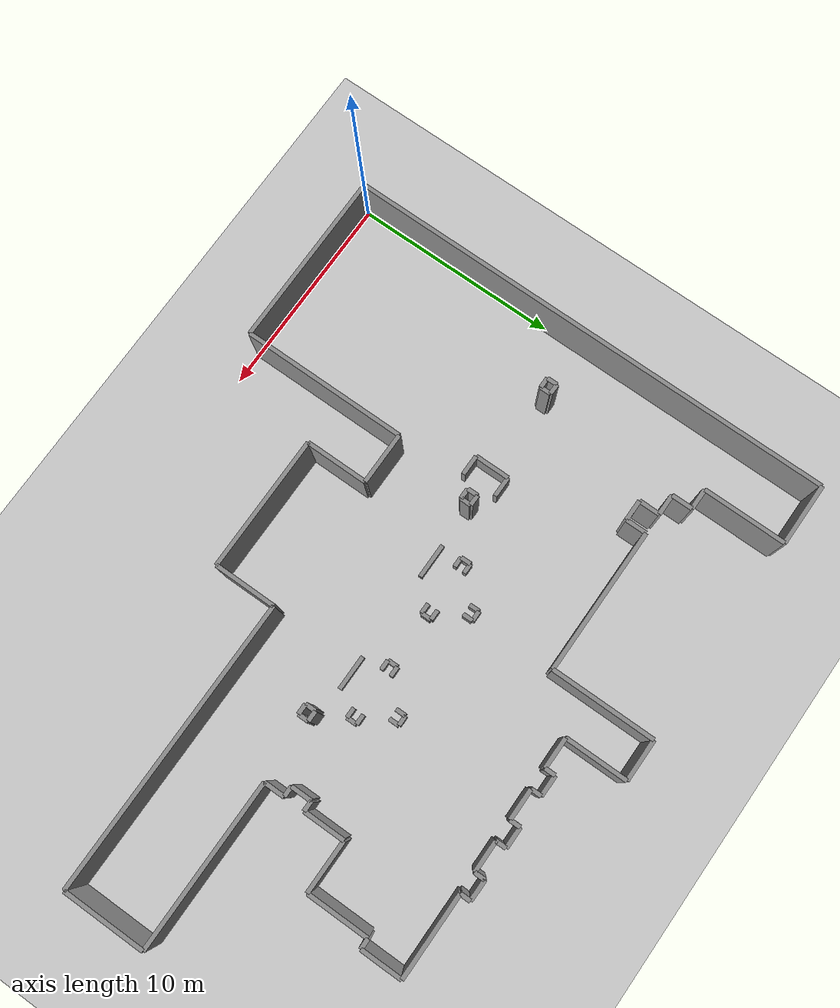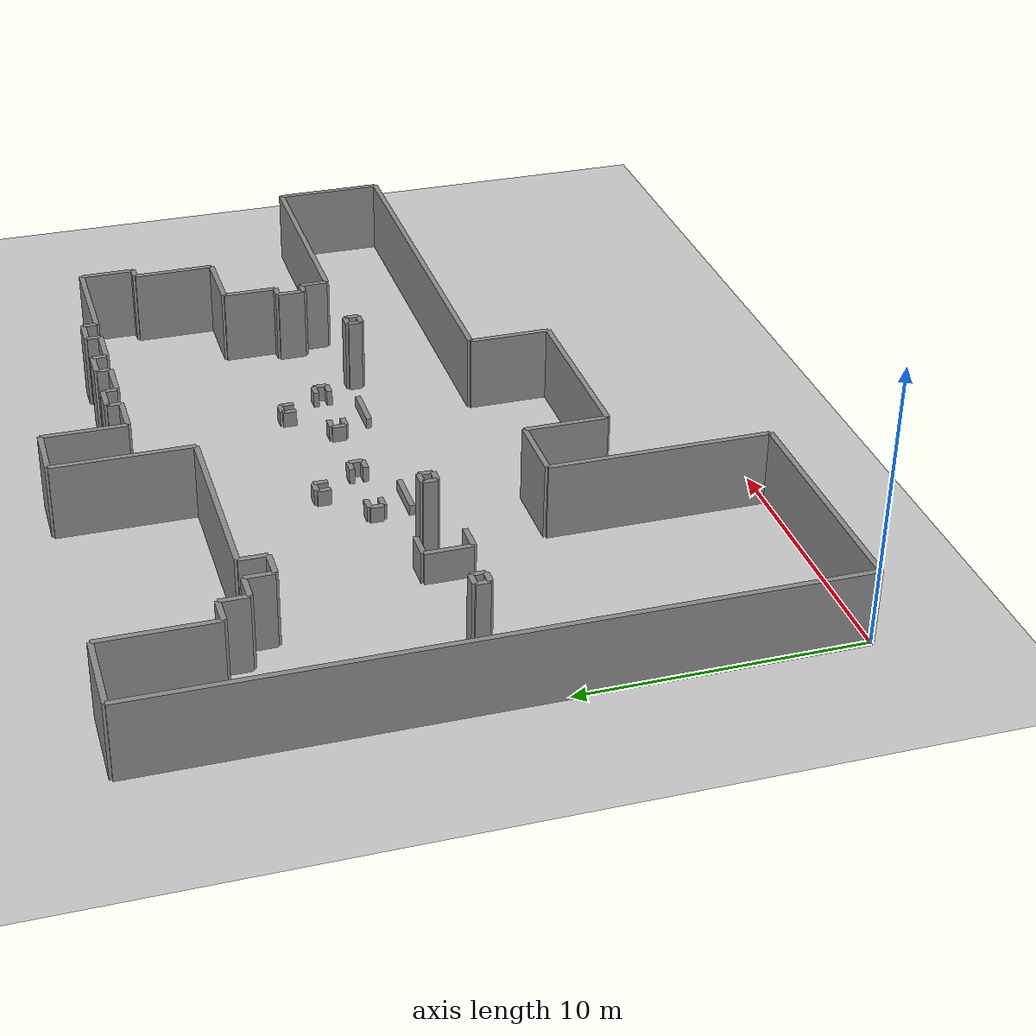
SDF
<?xml version="1.0" ?>

    <!-- this file is auto generated using pedsim_gazebo_plugin pkg -->
    <sdf version="1.5">
      <world name="default">
      <physics type="ode">
        <max_step_size>0.005</max_step_size>
        <real_time_factor>1.0</real_time_factor>
        <real_time_update_rate>200</real_time_update_rate>
      </physics>
      <plugin
        filename="libpedestrian_actor_motion_system.so"
        name="semantic_nav_gazebo::PedestrianActorMotionSystem">
      </plugin>
      <plugin
        filename="ignition-gazebo-physics-system"
        name="ignition::gazebo::systems::Physics">
      </plugin>
      <plugin
        filename="ignition-gazebo-user-commands-system"
        name="ignition::gazebo::systems::UserCommands">
      </plugin>
      <plugin
        filename="ignition-gazebo-scene-broadcaster-system"
        name="ignition::gazebo::systems::SceneBroadcaster">
      </plugin>
      <plugin
        filename="ignition-gazebo-sensors-system"
        name="ignition::gazebo::systems::Sensors">
        <render_engine>ogre2</render_engine>
      </plugin>

      <!-- Ground Plane -->

      <model name="ground_plane">
        <static>true</static>
        <link name="link">
          <collision name="collision">
            <geometry>
              <plane>
                <normal>0 0 1</normal>
                <size>100 100</size>
              </plane>
            </geometry>
          </collision>
          <visual name="visual">
            <geometry>
              <plane>
                <normal>0 0 1</normal>
                <size>100 100</size>
              </plane>
            </geometry>
            <material>
              <ambient>0.8 0.8 0.8 1</ambient>
              <diffuse>0.8 0.8 0.8 1</diffuse>
            </material>
          </visual>
        </link>
      </model>

      <light name="sun" type="directional">
        <cast_shadows>true</cast_shadows>
        <pose>0 0 10 0 0 0</pose>
        <diffuse>0.8 0.8 0.8 1</diffuse>
        <specular>0.2 0.2 0.2 1</specular>
        <attenuation>
          <range>1000</range>
          <constant>0.9</constant>
          <linear>0.01</linear>
          <quadratic>0.001</quadratic>
        </attenuation>
        <direction>-0.5 0.1 -0.9</direction>
      </light>

     <model name='grey_wall_1'>
      <static>1</static>
      <link name='link'>

	  <pose frame=''>0.0 12.0  1.4 0 0 1.57</pose>

        <collision name='collision'>
          <geometry>
            <box>

	     <size> 24.0 .2  2.8 </size>

      	   </box>
          </geometry>
          <max_contacts>10</max_contacts>
          <surface>
            <contact>
              <ode/>
            </contact>
            <bounce/>
            <friction>
              <torsional>
                <ode/>
              </torsional>
              <ode/>
            </friction>
          </surface>
        </collision>
        <visual name='visual'>
          <cast_shadows>0</cast_shadows>
          <geometry>
            <box>

	     <size> 24.0 .2  2.8 </size>

      	   </box>
       </geometry>
          <material>
            <ambient>0.55 0.55 0.55 1</ambient>
            <diffuse>0.55 0.55 0.55 1</diffuse>
          </material>
        </visual>
        <self_collide>0</self_collide>
        <enable_wind>0</enable_wind>
        <kinematic>0</kinematic>
      </link>
    </model>

     <model name='grey_wall_2'>
      <static>1</static>
      <link name='link'>

	  <pose frame=''>4.25 0.0  1.4 0 0 0.0</pose>

        <collision name='collision'>
          <geometry>
            <box>

	     <size> 8.5 .2  2.8 </size>

      	   </box>
          </geometry>
          <max_contacts>10</max_contacts>
          <surface>
            <contact>
              <ode/>
            </contact>
            <bounce/>
            <friction>
              <torsional>
                <ode/>
              </torsional>
              <ode/>
            </friction>
          </surface>
        </collision>
        <visual name='visual'>
          <cast_shadows>0</cast_shadows>
          <geometry>
            <box>

	     <size> 8.5 .2  2.8 </size>

      	   </box>
       </geometry>
          <material>
            <ambient>0.55 0.55 0.55 1</ambient>
            <diffuse>0.55 0.55 0.55 1</diffuse>
          </material>
        </visual>
        <self_collide>0</self_collide>
        <enable_wind>0</enable_wind>
        <kinematic>0</kinematic>
      </link>
    </model>

     <model name='grey_wall_3'>
      <static>1</static>
      <link name='link'>

	  <pose frame=''>8.5 4.0  1.4 0 0 1.57</pose>

        <collision name='collision'>
          <geometry>
            <box>

	     <size> 8.0 .2  2.8 </size>

      	   </box>
          </geometry>
          <max_contacts>10</max_contacts>
          <surface>
            <contact>
              <ode/>
            </contact>
            <bounce/>
            <friction>
              <torsional>
                <ode/>
              </torsional>
              <ode/>
            </friction>
          </surface>
        </collision>
        <visual name='visual'>
          <cast_shadows>0</cast_shadows>
          <geometry>
            <box>

	     <size> 8.0 .2  2.8 </size>

      	   </box>
       </geometry>
          <material>
            <ambient>0.55 0.55 0.55 1</ambient>
            <diffuse>0.55 0.55 0.55 1</diffuse>
          </material>
        </visual>
        <self_collide>0</self_collide>
        <enable_wind>0</enable_wind>
        <kinematic>0</kinematic>
      </link>
    </model>

     <model name='grey_wall_4'>
      <static>1</static>
      <link name='link'>

	  <pose frame=''>9.75 8.0  1.4 0 0 0.0</pose>

        <collision name='collision'>
          <geometry>
            <box>

	     <size> 2.5 .2  2.8 </size>

      	   </box>
          </geometry>
          <max_contacts>10</max_contacts>
          <surface>
            <contact>
              <ode/>
            </contact>
            <bounce/>
            <friction>
              <torsional>
                <ode/>
              </torsional>
              <ode/>
            </friction>
          </surface>
        </collision>
        <visual name='visual'>
          <cast_shadows>0</cast_shadows>
          <geometry>
            <box>

	     <size> 2.5 .2  2.8 </size>

      	   </box>
       </geometry>
          <material>
            <ambient>0.55 0.55 0.55 1</ambient>
            <diffuse>0.55 0.55 0.55 1</diffuse>
          </material>
        </visual>
        <self_collide>0</self_collide>
        <enable_wind>0</enable_wind>
        <kinematic>0</kinematic>
      </link>
    </model>

     <model name='grey_wall_5'>
      <static>1</static>
      <link name='link'>

	  <pose frame=''>11.0 6.5  1.4 0 0 1.57</pose>

        <collision name='collision'>
          <geometry>
            <box>

	     <size> 3.0 .2  2.8 </size>

      	   </box>
          </geometry>
          <max_contacts>10</max_contacts>
          <surface>
            <contact>
              <ode/>
            </contact>
            <bounce/>
            <friction>
              <torsional>
                <ode/>
              </torsional>
              <ode/>
            </friction>
          </surface>
        </collision>
        <visual name='visual'>
          <cast_shadows>0</cast_shadows>
          <geometry>
            <box>

	     <size> 3.0 .2  2.8 </size>

      	   </box>
       </geometry>
          <material>
            <ambient>0.55 0.55 0.55 1</ambient>
            <diffuse>0.55 0.55 0.55 1</diffuse>
          </material>
        </visual>
        <self_collide>0</self_collide>
        <enable_wind>0</enable_wind>
        <kinematic>0</kinematic>
      </link>
    </model>

     <model name='grey_wall_6'>
      <static>1</static>
      <link name='link'>

	  <pose frame=''>14.25 5.0  1.4 0 0 0.0</pose>

        <collision name='collision'>
          <geometry>
            <box>

	     <size> 6.5 .2  2.8 </size>

      	   </box>
          </geometry>
          <max_contacts>10</max_contacts>
          <surface>
            <contact>
              <ode/>
            </contact>
            <bounce/>
            <friction>
              <torsional>
                <ode/>
              </torsional>
              <ode/>
            </friction>
          </surface>
        </collision>
        <visual name='visual'>
          <cast_shadows>0</cast_shadows>
          <geometry>
            <box>

	     <size> 6.5 .2  2.8 </size>

      	   </box>
       </geometry>
          <material>
            <ambient>0.55 0.55 0.55 1</ambient>
            <diffuse>0.55 0.55 0.55 1</diffuse>
          </material>
        </visual>
        <self_collide>0</self_collide>
        <enable_wind>0</enable_wind>
        <kinematic>0</kinematic>
      </link>
    </model>

     <model name='grey_wall_7'>
      <static>1</static>
      <link name='link'>

	  <pose frame=''>17.5 6.5  1.4 0 0 1.57</pose>

        <collision name='collision'>
          <geometry>
            <box>

	     <size> 3.0 .2  2.8 </size>

      	   </box>
          </geometry>
          <max_contacts>10</max_contacts>
          <surface>
            <contact>
              <ode/>
            </contact>
            <bounce/>
            <friction>
              <torsional>
                <ode/>
              </torsional>
              <ode/>
            </friction>
          </surface>
        </collision>
        <visual name='visual'>
          <cast_shadows>0</cast_shadows>
          <geometry>
            <box>

	     <size> 3.0 .2  2.8 </size>

      	   </box>
       </geometry>
          <material>
            <ambient>0.55 0.55 0.55 1</ambient>
            <diffuse>0.55 0.55 0.55 1</diffuse>
          </material>
        </visual>
        <self_collide>0</self_collide>
        <enable_wind>0</enable_wind>
        <kinematic>0</kinematic>
      </link>
    </model>

     <model name='grey_wall_8'>
      <static>1</static>
      <link name='link'>

	  <pose frame=''>24.5 8.0  1.4 0 0 0.0</pose>

        <collision name='collision'>
          <geometry>
            <box>

	     <size> 14.0 .2  2.8 </size>

      	   </box>
          </geometry>
          <max_contacts>10</max_contacts>
          <surface>
            <contact>
              <ode/>
            </contact>
            <bounce/>
            <friction>
              <torsional>
                <ode/>
              </torsional>
              <ode/>
            </friction>
          </surface>
        </collision>
        <visual name='visual'>
          <cast_shadows>0</cast_shadows>
          <geometry>
            <box>

	     <size> 14.0 .2  2.8 </size>

      	   </box>
       </geometry>
          <material>
            <ambient>0.55 0.55 0.55 1</ambient>
            <diffuse>0.55 0.55 0.55 1</diffuse>
          </material>
        </visual>
        <self_collide>0</self_collide>
        <enable_wind>0</enable_wind>
        <kinematic>0</kinematic>
      </link>
    </model>

     <model name='grey_wall_9'>
      <static>1</static>
      <link name='link'>

	  <pose frame=''>31.5 10.0  1.4 0 0 1.57</pose>

        <collision name='collision'>
          <geometry>
            <box>

	     <size> 4.0 .2  2.8 </size>

      	   </box>
          </geometry>
          <max_contacts>10</max_contacts>
          <surface>
            <contact>
              <ode/>
            </contact>
            <bounce/>
            <friction>
              <torsional>
                <ode/>
              </torsional>
              <ode/>
            </friction>
          </surface>
        </collision>
        <visual name='visual'>
          <cast_shadows>0</cast_shadows>
          <geometry>
            <box>

	     <size> 4.0 .2  2.8 </size>

      	   </box>
       </geometry>
          <material>
            <ambient>0.55 0.55 0.55 1</ambient>
            <diffuse>0.55 0.55 0.55 1</diffuse>
          </material>
        </visual>
        <self_collide>0</self_collide>
        <enable_wind>0</enable_wind>
        <kinematic>0</kinematic>
      </link>
    </model>

     <model name='grey_wall_10'>
      <static>1</static>
      <link name='link'>

	  <pose frame=''>27.5 12.0  1.4 0 0 -0.0</pose>

        <collision name='collision'>
          <geometry>
            <box>

	     <size> 8.0 .2  2.8 </size>

      	   </box>
          </geometry>
          <max_contacts>10</max_contacts>
          <surface>
            <contact>
              <ode/>
            </contact>
            <bounce/>
            <friction>
              <torsional>
                <ode/>
              </torsional>
              <ode/>
            </friction>
          </surface>
        </collision>
        <visual name='visual'>
          <cast_shadows>0</cast_shadows>
          <geometry>
            <box>

	     <size> 8.0 .2  2.8 </size>

      	   </box>
       </geometry>
          <material>
            <ambient>0.55 0.55 0.55 1</ambient>
            <diffuse>0.55 0.55 0.55 1</diffuse>
          </material>
        </visual>
        <self_collide>0</self_collide>
        <enable_wind>0</enable_wind>
        <kinematic>0</kinematic>
      </link>
    </model>

     <model name='grey_wall_11'>
      <static>1</static>
      <link name='link'>

	  <pose frame=''>23.5 12.5  1.4 0 0 1.57</pose>

        <collision name='collision'>
          <geometry>
            <box>

	     <size> 1.0 .2  2.8 </size>

      	   </box>
          </geometry>
          <max_contacts>10</max_contacts>
          <surface>
            <contact>
              <ode/>
            </contact>
            <bounce/>
            <friction>
              <torsional>
                <ode/>
              </torsional>
              <ode/>
            </friction>
          </surface>
        </collision>
        <visual name='visual'>
          <cast_shadows>0</cast_shadows>
          <geometry>
            <box>

	     <size> 1.0 .2  2.8 </size>

      	   </box>
       </geometry>
          <material>
            <ambient>0.55 0.55 0.55 1</ambient>
            <diffuse>0.55 0.55 0.55 1</diffuse>
          </material>
        </visual>
        <self_collide>0</self_collide>
        <enable_wind>0</enable_wind>
        <kinematic>0</kinematic>
      </link>
    </model>

     <model name='grey_wall_12'>
      <static>1</static>
      <link name='link'>

	  <pose frame=''>23.25 13.0  1.4 0 0 -0.0</pose>

        <collision name='collision'>
          <geometry>
            <box>

	     <size> 0.5 .2  2.8 </size>

      	   </box>
          </geometry>
          <max_contacts>10</max_contacts>
          <surface>
            <contact>
              <ode/>
            </contact>
            <bounce/>
            <friction>
              <torsional>
                <ode/>
              </torsional>
              <ode/>
            </friction>
          </surface>
        </collision>
        <visual name='visual'>
          <cast_shadows>0</cast_shadows>
          <geometry>
            <box>

	     <size> 0.5 .2  2.8 </size>

      	   </box>
       </geometry>
          <material>
            <ambient>0.55 0.55 0.55 1</ambient>
            <diffuse>0.55 0.55 0.55 1</diffuse>
          </material>
        </visual>
        <self_collide>0</self_collide>
        <enable_wind>0</enable_wind>
        <kinematic>0</kinematic>
      </link>
    </model>

     <model name='grey_wall_13'>
      <static>1</static>
      <link name='link'>

	  <pose frame=''>23.0 13.5  1.4 0 0 1.57</pose>

        <collision name='collision'>
          <geometry>
            <box>

	     <size> 1.0 .2  2.8 </size>

      	   </box>
          </geometry>
          <max_contacts>10</max_contacts>
          <surface>
            <contact>
              <ode/>
            </contact>
            <bounce/>
            <friction>
              <torsional>
                <ode/>
              </torsional>
              <ode/>
            </friction>
          </surface>
        </collision>
        <visual name='visual'>
          <cast_shadows>0</cast_shadows>
          <geometry>
            <box>

	     <size> 1.0 .2  2.8 </size>

      	   </box>
       </geometry>
          <material>
            <ambient>0.55 0.55 0.55 1</ambient>
            <diffuse>0.55 0.55 0.55 1</diffuse>
          </material>
        </visual>
        <self_collide>0</self_collide>
        <enable_wind>0</enable_wind>
        <kinematic>0</kinematic>
      </link>
    </model>

     <model name='grey_wall_14'>
      <static>1</static>
      <link name='link'>

	  <pose frame=''>23.25 14.0  1.4 0 0 0.0</pose>

        <collision name='collision'>
          <geometry>
            <box>

	     <size> 0.5 .2  2.8 </size>

      	   </box>
          </geometry>
          <max_contacts>10</max_contacts>
          <surface>
            <contact>
              <ode/>
            </contact>
            <bounce/>
            <friction>
              <torsional>
                <ode/>
              </torsional>
              <ode/>
            </friction>
          </surface>
        </collision>
        <visual name='visual'>
          <cast_shadows>0</cast_shadows>
          <geometry>
            <box>

	     <size> 0.5 .2  2.8 </size>

      	   </box>
       </geometry>
          <material>
            <ambient>0.55 0.55 0.55 1</ambient>
            <diffuse>0.55 0.55 0.55 1</diffuse>
          </material>
        </visual>
        <self_collide>0</self_collide>
        <enable_wind>0</enable_wind>
        <kinematic>0</kinematic>
      </link>
    </model>

     <model name='grey_wall_15'>
      <static>1</static>
      <link name='link'>

	  <pose frame=''>23.5 15.0  1.4 0 0 1.57</pose>

        <collision name='collision'>
          <geometry>
            <box>

	     <size> 2.0 .2  2.8 </size>

      	   </box>
          </geometry>
          <max_contacts>10</max_contacts>
          <surface>
            <contact>
              <ode/>
            </contact>
            <bounce/>
            <friction>
              <torsional>
                <ode/>
              </torsional>
              <ode/>
            </friction>
          </surface>
        </collision>
        <visual name='visual'>
          <cast_shadows>0</cast_shadows>
          <geometry>
            <box>

	     <size> 2.0 .2  2.8 </size>

      	   </box>
       </geometry>
          <material>
            <ambient>0.55 0.55 0.55 1</ambient>
            <diffuse>0.55 0.55 0.55 1</diffuse>
          </material>
        </visual>
        <self_collide>0</self_collide>
        <enable_wind>0</enable_wind>
        <kinematic>0</kinematic>
      </link>
    </model>

     <model name='grey_wall_16'>
      <static>1</static>
      <link name='link'>

	  <pose frame=''>24.75 16.0  1.4 0 0 0.0</pose>

        <collision name='collision'>
          <geometry>
            <box>

	     <size> 2.5 .2  2.8 </size>

      	   </box>
          </geometry>
          <max_contacts>10</max_contacts>
          <surface>
            <contact>
              <ode/>
            </contact>
            <bounce/>
            <friction>
              <torsional>
                <ode/>
              </torsional>
              <ode/>
            </friction>
          </surface>
        </collision>
        <visual name='visual'>
          <cast_shadows>0</cast_shadows>
          <geometry>
            <box>

	     <size> 2.5 .2  2.8 </size>

      	   </box>
       </geometry>
          <material>
            <ambient>0.55 0.55 0.55 1</ambient>
            <diffuse>0.55 0.55 0.55 1</diffuse>
          </material>
        </visual>
        <self_collide>0</self_collide>
        <enable_wind>0</enable_wind>
        <kinematic>0</kinematic>
      </link>
    </model>

     <model name='grey_wall_17'>
      <static>1</static>
      <link name='link'>

	  <pose frame=''>26.0 17.5  1.4 0 0 1.57</pose>

        <collision name='collision'>
          <geometry>
            <box>

	     <size> 3.0 .2  2.8 </size>

      	   </box>
          </geometry>
          <max_contacts>10</max_contacts>
          <surface>
            <contact>
              <ode/>
            </contact>
            <bounce/>
            <friction>
              <torsional>
                <ode/>
              </torsional>
              <ode/>
            </friction>
          </surface>
        </collision>
        <visual name='visual'>
          <cast_shadows>0</cast_shadows>
          <geometry>
            <box>

	     <size> 3.0 .2  2.8 </size>

      	   </box>
       </geometry>
          <material>
            <ambient>0.55 0.55 0.55 1</ambient>
            <diffuse>0.55 0.55 0.55 1</diffuse>
          </material>
        </visual>
        <self_collide>0</self_collide>
        <enable_wind>0</enable_wind>
        <kinematic>0</kinematic>
      </link>
    </model>

     <model name='grey_wall_18'>
      <static>1</static>
      <link name='link'>

	  <pose frame=''>26.25 19.0  1.4 0 0 0.0</pose>

        <collision name='collision'>
          <geometry>
            <box>

	     <size> 0.5 .2  2.8 </size>

      	   </box>
          </geometry>
          <max_contacts>10</max_contacts>
          <surface>
            <contact>
              <ode/>
            </contact>
            <bounce/>
            <friction>
              <torsional>
                <ode/>
              </torsional>
              <ode/>
            </friction>
          </surface>
        </collision>
        <visual name='visual'>
          <cast_shadows>0</cast_shadows>
          <geometry>
            <box>

	     <size> 0.5 .2  2.8 </size>

      	   </box>
       </geometry>
          <material>
            <ambient>0.55 0.55 0.55 1</ambient>
            <diffuse>0.55 0.55 0.55 1</diffuse>
          </material>
        </visual>
        <self_collide>0</self_collide>
        <enable_wind>0</enable_wind>
        <kinematic>0</kinematic>
      </link>
    </model>

     <model name='grey_wall_19'>
      <static>1</static>
      <link name='link'>

	  <pose frame=''>26.5 20.0  1.4 0 0 1.57</pose>

        <collision name='collision'>
          <geometry>
            <box>

	     <size> 2.0 .2  2.8 </size>

      	   </box>
          </geometry>
          <max_contacts>10</max_contacts>
          <surface>
            <contact>
              <ode/>
            </contact>
            <bounce/>
            <friction>
              <torsional>
                <ode/>
              </torsional>
              <ode/>
            </friction>
          </surface>
        </collision>
        <visual name='visual'>
          <cast_shadows>0</cast_shadows>
          <geometry>
            <box>

	     <size> 2.0 .2  2.8 </size>

      	   </box>
       </geometry>
          <material>
            <ambient>0.55 0.55 0.55 1</ambient>
            <diffuse>0.55 0.55 0.55 1</diffuse>
          </material>
        </visual>
        <self_collide>0</self_collide>
        <enable_wind>0</enable_wind>
        <kinematic>0</kinematic>
      </link>
    </model>

     <model name='grey_wall_20'>
      <static>1</static>
      <link name='link'>

	  <pose frame=''>24.5 21.0  1.4 0 0 -0.0</pose>

        <collision name='collision'>
          <geometry>
            <box>

	     <size> 4.0 .2  2.8 </size>

      	   </box>
          </geometry>
          <max_contacts>10</max_contacts>
          <surface>
            <contact>
              <ode/>
            </contact>
            <bounce/>
            <friction>
              <torsional>
                <ode/>
              </torsional>
              <ode/>
            </friction>
          </surface>
        </collision>
        <visual name='visual'>
          <cast_shadows>0</cast_shadows>
          <geometry>
            <box>

	     <size> 4.0 .2  2.8 </size>

      	   </box>
       </geometry>
          <material>
            <ambient>0.55 0.55 0.55 1</ambient>
            <diffuse>0.55 0.55 0.55 1</diffuse>
          </material>
        </visual>
        <self_collide>0</self_collide>
        <enable_wind>0</enable_wind>
        <kinematic>0</kinematic>
      </link>
    </model>

     <model name='grey_wall_21'>
      <static>1</static>
      <link name='link'>

	  <pose frame=''>22.5 21.25  1.4 0 0 1.57</pose>

        <collision name='collision'>
          <geometry>
            <box>

	     <size> 0.5 .2  2.8 </size>

      	   </box>
          </geometry>
          <max_contacts>10</max_contacts>
          <surface>
            <contact>
              <ode/>
            </contact>
            <bounce/>
            <friction>
              <torsional>
                <ode/>
              </torsional>
              <ode/>
            </friction>
          </surface>
        </collision>
        <visual name='visual'>
          <cast_shadows>0</cast_shadows>
          <geometry>
            <box>

	     <size> 0.5 .2  2.8 </size>

      	   </box>
       </geometry>
          <material>
            <ambient>0.55 0.55 0.55 1</ambient>
            <diffuse>0.55 0.55 0.55 1</diffuse>
          </material>
        </visual>
        <self_collide>0</self_collide>
        <enable_wind>0</enable_wind>
        <kinematic>0</kinematic>
      </link>
    </model>

     <model name='grey_wall_22'>
      <static>1</static>
      <link name='link'>

	  <pose frame=''>22.0 21.5  1.4 0 0 -0.0</pose>

        <collision name='collision'>
          <geometry>
            <box>

	     <size> 1.0 .2  2.8 </size>

      	   </box>
          </geometry>
          <max_contacts>10</max_contacts>
          <surface>
            <contact>
              <ode/>
            </contact>
            <bounce/>
            <friction>
              <torsional>
                <ode/>
              </torsional>
              <ode/>
            </friction>
          </surface>
        </collision>
        <visual name='visual'>
          <cast_shadows>0</cast_shadows>
          <geometry>
            <box>

	     <size> 1.0 .2  2.8 </size>

      	   </box>
       </geometry>
          <material>
            <ambient>0.55 0.55 0.55 1</ambient>
            <diffuse>0.55 0.55 0.55 1</diffuse>
          </material>
        </visual>
        <self_collide>0</self_collide>
        <enable_wind>0</enable_wind>
        <kinematic>0</kinematic>
      </link>
    </model>

     <model name='grey_wall_23'>
      <static>1</static>
      <link name='link'>

	  <pose frame=''>21.5 21.25  1.4 0 0 1.57</pose>

        <collision name='collision'>
          <geometry>
            <box>

	     <size> 0.5 .2  2.8 </size>

      	   </box>
          </geometry>
          <max_contacts>10</max_contacts>
          <surface>
            <contact>
              <ode/>
            </contact>
            <bounce/>
            <friction>
              <torsional>
                <ode/>
              </torsional>
              <ode/>
            </friction>
          </surface>
        </collision>
        <visual name='visual'>
          <cast_shadows>0</cast_shadows>
          <geometry>
            <box>

	     <size> 0.5 .2  2.8 </size>

      	   </box>
       </geometry>
          <material>
            <ambient>0.55 0.55 0.55 1</ambient>
            <diffuse>0.55 0.55 0.55 1</diffuse>
          </material>
        </visual>
        <self_collide>0</self_collide>
        <enable_wind>0</enable_wind>
        <kinematic>0</kinematic>
      </link>
    </model>

     <model name='grey_wall_24'>
      <static>1</static>
      <link name='link'>

	  <pose frame=''>20.75 21.0  1.4 0 0 -0.0</pose>

        <collision name='collision'>
          <geometry>
            <box>

	     <size> 1.5 .2  2.8 </size>

      	   </box>
          </geometry>
          <max_contacts>10</max_contacts>
          <surface>
            <contact>
              <ode/>
            </contact>
            <bounce/>
            <friction>
              <torsional>
                <ode/>
              </torsional>
              <ode/>
            </friction>
          </surface>
        </collision>
        <visual name='visual'>
          <cast_shadows>0</cast_shadows>
          <geometry>
            <box>

	     <size> 1.5 .2  2.8 </size>

      	   </box>
       </geometry>
          <material>
            <ambient>0.55 0.55 0.55 1</ambient>
            <diffuse>0.55 0.55 0.55 1</diffuse>
          </material>
        </visual>
        <self_collide>0</self_collide>
        <enable_wind>0</enable_wind>
        <kinematic>0</kinematic>
      </link>
    </model>

     <model name='grey_wall_25'>
      <static>1</static>
      <link name='link'>

	  <pose frame=''>20.0 21.25  1.4 0 0 1.57</pose>

        <collision name='collision'>
          <geometry>
            <box>

	     <size> 0.5 .2  2.8 </size>

      	   </box>
          </geometry>
          <max_contacts>10</max_contacts>
          <surface>
            <contact>
              <ode/>
            </contact>
            <bounce/>
            <friction>
              <torsional>
                <ode/>
              </torsional>
              <ode/>
            </friction>
          </surface>
        </collision>
        <visual name='visual'>
          <cast_shadows>0</cast_shadows>
          <geometry>
            <box>

	     <size> 0.5 .2  2.8 </size>

      	   </box>
       </geometry>
          <material>
            <ambient>0.55 0.55 0.55 1</ambient>
            <diffuse>0.55 0.55 0.55 1</diffuse>
          </material>
        </visual>
        <self_collide>0</self_collide>
        <enable_wind>0</enable_wind>
        <kinematic>0</kinematic>
      </link>
    </model>

     <model name='grey_wall_26'>
      <static>1</static>
      <link name='link'>

	  <pose frame=''>19.5 21.5  1.4 0 0 -0.0</pose>

        <collision name='collision'>
          <geometry>
            <box>

	     <size> 1.0 .2  2.8 </size>

      	   </box>
          </geometry>
          <max_contacts>10</max_contacts>
          <surface>
            <contact>
              <ode/>
            </contact>
            <bounce/>
            <friction>
              <torsional>
                <ode/>
              </torsional>
              <ode/>
            </friction>
          </surface>
        </collision>
        <visual name='visual'>
          <cast_shadows>0</cast_shadows>
          <geometry>
            <box>

	     <size> 1.0 .2  2.8 </size>

      	   </box>
       </geometry>
          <material>
            <ambient>0.55 0.55 0.55 1</ambient>
            <diffuse>0.55 0.55 0.55 1</diffuse>
          </material>
        </visual>
        <self_collide>0</self_collide>
        <enable_wind>0</enable_wind>
        <kinematic>0</kinematic>
      </link>
    </model>

     <model name='grey_wall_27'>
      <static>1</static>
      <link name='link'>

	  <pose frame=''>19.0 21.25  1.4 0 0 1.57</pose>

        <collision name='collision'>
          <geometry>
            <box>

	     <size> 0.5 .2  2.8 </size>

      	   </box>
          </geometry>
          <max_contacts>10</max_contacts>
          <surface>
            <contact>
              <ode/>
            </contact>
            <bounce/>
            <friction>
              <torsional>
                <ode/>
              </torsional>
              <ode/>
            </friction>
          </surface>
        </collision>
        <visual name='visual'>
          <cast_shadows>0</cast_shadows>
          <geometry>
            <box>

	     <size> 0.5 .2  2.8 </size>

      	   </box>
       </geometry>
          <material>
            <ambient>0.55 0.55 0.55 1</ambient>
            <diffuse>0.55 0.55 0.55 1</diffuse>
          </material>
        </visual>
        <self_collide>0</self_collide>
        <enable_wind>0</enable_wind>
        <kinematic>0</kinematic>
      </link>
    </model>

     <model name='grey_wall_28'>
      <static>1</static>
      <link name='link'>

	  <pose frame=''>18.25 21.0  1.4 0 0 -0.0</pose>

        <collision name='collision'>
          <geometry>
            <box>

	     <size> 1.5 .2  2.8 </size>

      	   </box>
          </geometry>
          <max_contacts>10</max_contacts>
          <surface>
            <contact>
              <ode/>
            </contact>
            <bounce/>
            <friction>
              <torsional>
                <ode/>
              </torsional>
              <ode/>
            </friction>
          </surface>
        </collision>
        <visual name='visual'>
          <cast_shadows>0</cast_shadows>
          <geometry>
            <box>

	     <size> 1.5 .2  2.8 </size>

      	   </box>
       </geometry>
          <material>
            <ambient>0.55 0.55 0.55 1</ambient>
            <diffuse>0.55 0.55 0.55 1</diffuse>
          </material>
        </visual>
        <self_collide>0</self_collide>
        <enable_wind>0</enable_wind>
        <kinematic>0</kinematic>
      </link>
    </model>

     <model name='grey_wall_29'>
      <static>1</static>
      <link name='link'>

	  <pose frame=''>17.5 21.25  1.4 0 0 1.57</pose>

        <collision name='collision'>
          <geometry>
            <box>

	     <size> 0.5 .2  2.8 </size>

      	   </box>
          </geometry>
          <max_contacts>10</max_contacts>
          <surface>
            <contact>
              <ode/>
            </contact>
            <bounce/>
            <friction>
              <torsional>
                <ode/>
              </torsional>
              <ode/>
            </friction>
          </surface>
        </collision>
        <visual name='visual'>
          <cast_shadows>0</cast_shadows>
          <geometry>
            <box>

	     <size> 0.5 .2  2.8 </size>

      	   </box>
       </geometry>
          <material>
            <ambient>0.55 0.55 0.55 1</ambient>
            <diffuse>0.55 0.55 0.55 1</diffuse>
          </material>
        </visual>
        <self_collide>0</self_collide>
        <enable_wind>0</enable_wind>
        <kinematic>0</kinematic>
      </link>
    </model>

     <model name='grey_wall_30'>
      <static>1</static>
      <link name='link'>

	  <pose frame=''>17.0 21.5  1.4 0 0 -0.0</pose>

        <collision name='collision'>
          <geometry>
            <box>

	     <size> 1.0 .2  2.8 </size>

      	   </box>
          </geometry>
          <max_contacts>10</max_contacts>
          <surface>
            <contact>
              <ode/>
            </contact>
            <bounce/>
            <friction>
              <torsional>
                <ode/>
              </torsional>
              <ode/>
            </friction>
          </surface>
        </collision>
        <visual name='visual'>
          <cast_shadows>0</cast_shadows>
          <geometry>
            <box>

	     <size> 1.0 .2  2.8 </size>

      	   </box>
       </geometry>
          <material>
            <ambient>0.55 0.55 0.55 1</ambient>
            <diffuse>0.55 0.55 0.55 1</diffuse>
          </material>
        </visual>
        <self_collide>0</self_collide>
        <enable_wind>0</enable_wind>
        <kinematic>0</kinematic>
      </link>
    </model>

     <model name='grey_wall_31'>
      <static>1</static>
      <link name='link'>

	  <pose frame=''>16.5 21.25  1.4 0 0 1.57</pose>

        <collision name='collision'>
          <geometry>
            <box>

	     <size> 0.5 .2  2.8 </size>

      	   </box>
          </geometry>
          <max_contacts>10</max_contacts>
          <surface>
            <contact>
              <ode/>
            </contact>
            <bounce/>
            <friction>
              <torsional>
                <ode/>
              </torsional>
              <ode/>
            </friction>
          </surface>
        </collision>
        <visual name='visual'>
          <cast_shadows>0</cast_shadows>
          <geometry>
            <box>

	     <size> 0.5 .2  2.8 </size>

      	   </box>
       </geometry>
          <material>
            <ambient>0.55 0.55 0.55 1</ambient>
            <diffuse>0.55 0.55 0.55 1</diffuse>
          </material>
        </visual>
        <self_collide>0</self_collide>
        <enable_wind>0</enable_wind>
        <kinematic>0</kinematic>
      </link>
    </model>

     <model name='grey_wall_32'>
      <static>1</static>
      <link name='link'>

	  <pose frame=''>15.75 21.0  1.4 0 0 -0.0</pose>

        <collision name='collision'>
          <geometry>
            <box>

	     <size> 1.5 .2  2.8 </size>

      	   </box>
          </geometry>
          <max_contacts>10</max_contacts>
          <surface>
            <contact>
              <ode/>
            </contact>
            <bounce/>
            <friction>
              <torsional>
                <ode/>
              </torsional>
              <ode/>
            </friction>
          </surface>
        </collision>
        <visual name='visual'>
          <cast_shadows>0</cast_shadows>
          <geometry>
            <box>

	     <size> 1.5 .2  2.8 </size>

      	   </box>
       </geometry>
          <material>
            <ambient>0.55 0.55 0.55 1</ambient>
            <diffuse>0.55 0.55 0.55 1</diffuse>
          </material>
        </visual>
        <self_collide>0</self_collide>
        <enable_wind>0</enable_wind>
        <kinematic>0</kinematic>
      </link>
    </model>

     <model name='grey_wall_33'>
      <static>1</static>
      <link name='link'>

	  <pose frame=''>15.0 22.5  1.4 0 0 1.57</pose>

        <collision name='collision'>
          <geometry>
            <box>

	     <size> 3.0 .2  2.8 </size>

      	   </box>
          </geometry>
          <max_contacts>10</max_contacts>
          <surface>
            <contact>
              <ode/>
            </contact>
            <bounce/>
            <friction>
              <torsional>
                <ode/>
              </torsional>
              <ode/>
            </friction>
          </surface>
        </collision>
        <visual name='visual'>
          <cast_shadows>0</cast_shadows>
          <geometry>
            <box>

	     <size> 3.0 .2  2.8 </size>

      	   </box>
       </geometry>
          <material>
            <ambient>0.55 0.55 0.55 1</ambient>
            <diffuse>0.55 0.55 0.55 1</diffuse>
          </material>
        </visual>
        <self_collide>0</self_collide>
        <enable_wind>0</enable_wind>
        <kinematic>0</kinematic>
      </link>
    </model>

     <model name='grey_wall_34'>
      <static>1</static>
      <link name='link'>

	  <pose frame=''>14.0 24.0  1.4 0 0 -0.0</pose>

        <collision name='collision'>
          <geometry>
            <box>

	     <size> 2.0 .2  2.8 </size>

      	   </box>
          </geometry>
          <max_contacts>10</max_contacts>
          <surface>
            <contact>
              <ode/>
            </contact>
            <bounce/>
            <friction>
              <torsional>
                <ode/>
              </torsional>
              <ode/>
            </friction>
          </surface>
        </collision>
        <visual name='visual'>
          <cast_shadows>0</cast_shadows>
          <geometry>
            <box>

	     <size> 2.0 .2  2.8 </size>

      	   </box>
       </geometry>
          <material>
            <ambient>0.55 0.55 0.55 1</ambient>
            <diffuse>0.55 0.55 0.55 1</diffuse>
          </material>
        </visual>
        <self_collide>0</self_collide>
        <enable_wind>0</enable_wind>
        <kinematic>0</kinematic>
      </link>
    </model>

     <model name='grey_wall_35'>
      <static>1</static>
      <link name='link'>

	  <pose frame=''>13.0 21.5  1.4 0 0 1.57</pose>

        <collision name='collision'>
          <geometry>
            <box>

	     <size> 5.0 .2  2.8 </size>

      	   </box>
          </geometry>
          <max_contacts>10</max_contacts>
          <surface>
            <contact>
              <ode/>
            </contact>
            <bounce/>
            <friction>
              <torsional>
                <ode/>
              </torsional>
              <ode/>
            </friction>
          </surface>
        </collision>
        <visual name='visual'>
          <cast_shadows>0</cast_shadows>
          <geometry>
            <box>

	     <size> 5.0 .2  2.8 </size>

      	   </box>
       </geometry>
          <material>
            <ambient>0.55 0.55 0.55 1</ambient>
            <diffuse>0.55 0.55 0.55 1</diffuse>
          </material>
        </visual>
        <self_collide>0</self_collide>
        <enable_wind>0</enable_wind>
        <kinematic>0</kinematic>
      </link>
    </model>

     <model name='grey_wall_36'>
      <static>1</static>
      <link name='link'>

	  <pose frame=''>9.5 19.0  1.4 0 0 -0.0</pose>

        <collision name='collision'>
          <geometry>
            <box>

	     <size> 7.0 .2  2.8 </size>

      	   </box>
          </geometry>
          <max_contacts>10</max_contacts>
          <surface>
            <contact>
              <ode/>
            </contact>
            <bounce/>
            <friction>
              <torsional>
                <ode/>
              </torsional>
              <ode/>
            </friction>
          </surface>
        </collision>
        <visual name='visual'>
          <cast_shadows>0</cast_shadows>
          <geometry>
            <box>

	     <size> 7.0 .2  2.8 </size>

      	   </box>
       </geometry>
          <material>
            <ambient>0.55 0.55 0.55 1</ambient>
            <diffuse>0.55 0.55 0.55 1</diffuse>
          </material>
        </visual>
        <self_collide>0</self_collide>
        <enable_wind>0</enable_wind>
        <kinematic>0</kinematic>
      </link>
    </model>

     <model name='grey_wall_37'>
      <static>1</static>
      <link name='link'>

	  <pose frame=''>6.0 18.5  1.4 0 0 1.57</pose>

        <collision name='collision'>
          <geometry>
            <box>

	     <size> 1.0 .2  2.8 </size>

      	   </box>
          </geometry>
          <max_contacts>10</max_contacts>
          <surface>
            <contact>
              <ode/>
            </contact>
            <bounce/>
            <friction>
              <torsional>
                <ode/>
              </torsional>
              <ode/>
            </friction>
          </surface>
        </collision>
        <visual name='visual'>
          <cast_shadows>0</cast_shadows>
          <geometry>
            <box>

	     <size> 1.0 .2  2.8 </size>

      	   </box>
       </geometry>
          <material>
            <ambient>0.55 0.55 0.55 1</ambient>
            <diffuse>0.55 0.55 0.55 1</diffuse>
          </material>
        </visual>
        <self_collide>0</self_collide>
        <enable_wind>0</enable_wind>
        <kinematic>0</kinematic>
      </link>
    </model>

     <model name='grey_wall_38'>
      <static>1</static>
      <link name='link'>

	  <pose frame=''>5.5 18.0  1.4 0 0 -0.0</pose>

        <collision name='collision'>
          <geometry>
            <box>

	     <size> 1.0 .2  2.8 </size>

      	   </box>
          </geometry>
          <max_contacts>10</max_contacts>
          <surface>
            <contact>
              <ode/>
            </contact>
            <bounce/>
            <friction>
              <torsional>
                <ode/>
              </torsional>
              <ode/>
            </friction>
          </surface>
        </collision>
        <visual name='visual'>
          <cast_shadows>0</cast_shadows>
          <geometry>
            <box>

	     <size> 1.0 .2  2.8 </size>

      	   </box>
       </geometry>
          <material>
            <ambient>0.55 0.55 0.55 1</ambient>
            <diffuse>0.55 0.55 0.55 1</diffuse>
          </material>
        </visual>
        <self_collide>0</self_collide>
        <enable_wind>0</enable_wind>
        <kinematic>0</kinematic>
      </link>
    </model>

     <model name='grey_wall_39'>
      <static>1</static>
      <link name='link'>

	  <pose frame=''>5.0 18.5  1.4 0 0 1.57</pose>

        <collision name='collision'>
          <geometry>
            <box>

	     <size> 1.0 .2  2.8 </size>

      	   </box>
          </geometry>
          <max_contacts>10</max_contacts>
          <surface>
            <contact>
              <ode/>
            </contact>
            <bounce/>
            <friction>
              <torsional>
                <ode/>
              </torsional>
              <ode/>
            </friction>
          </surface>
        </collision>
        <visual name='visual'>
          <cast_shadows>0</cast_shadows>
          <geometry>
            <box>

	     <size> 1.0 .2  2.8 </size>

      	   </box>
       </geometry>
          <material>
            <ambient>0.55 0.55 0.55 1</ambient>
            <diffuse>0.55 0.55 0.55 1</diffuse>
          </material>
        </visual>
        <self_collide>0</self_collide>
        <enable_wind>0</enable_wind>
        <kinematic>0</kinematic>
      </link>
    </model>

     <model name='grey_wall_40'>
      <static>1</static>
      <link name='link'>

	  <pose frame=''>4.5 19.0  1.4 0 0 -0.0</pose>

        <collision name='collision'>
          <geometry>
            <box>

	     <size> 1.0 .2  2.8 </size>

      	   </box>
          </geometry>
          <max_contacts>10</max_contacts>
          <surface>
            <contact>
              <ode/>
            </contact>
            <bounce/>
            <friction>
              <torsional>
                <ode/>
              </torsional>
              <ode/>
            </friction>
          </surface>
        </collision>
        <visual name='visual'>
          <cast_shadows>0</cast_shadows>
          <geometry>
            <box>

	     <size> 1.0 .2  2.8 </size>

      	   </box>
       </geometry>
          <material>
            <ambient>0.55 0.55 0.55 1</ambient>
            <diffuse>0.55 0.55 0.55 1</diffuse>
          </material>
        </visual>
        <self_collide>0</self_collide>
        <enable_wind>0</enable_wind>
        <kinematic>0</kinematic>
      </link>
    </model>

     <model name='grey_wall_41'>
      <static>1</static>
      <link name='link'>

	  <pose frame=''>4.0 19.5  1.4 0 0 1.57</pose>

        <collision name='collision'>
          <geometry>
            <box>

	     <size> 1.0 .2  2.8 </size>

      	   </box>
          </geometry>
          <max_contacts>10</max_contacts>
          <surface>
            <contact>
              <ode/>
            </contact>
            <bounce/>
            <friction>
              <torsional>
                <ode/>
              </torsional>
              <ode/>
            </friction>
          </surface>
        </collision>
        <visual name='visual'>
          <cast_shadows>0</cast_shadows>
          <geometry>
            <box>

	     <size> 1.0 .2  2.8 </size>

      	   </box>
       </geometry>
          <material>
            <ambient>0.55 0.55 0.55 1</ambient>
            <diffuse>0.55 0.55 0.55 1</diffuse>
          </material>
        </visual>
        <self_collide>0</self_collide>
        <enable_wind>0</enable_wind>
        <kinematic>0</kinematic>
      </link>
    </model>

     <model name='grey_wall_42'>
      <static>1</static>
      <link name='link'>

	  <pose frame=''>3.5 20.0  1.4 0 0 -0.0</pose>

        <collision name='collision'>
          <geometry>
            <box>

	     <size> 1.0 .2  2.8 </size>

      	   </box>
          </geometry>
          <max_contacts>10</max_contacts>
          <surface>
            <contact>
              <ode/>
            </contact>
            <bounce/>
            <friction>
              <torsional>
                <ode/>
              </torsional>
              <ode/>
            </friction>
          </surface>
        </collision>
        <visual name='visual'>
          <cast_shadows>0</cast_shadows>
          <geometry>
            <box>

	     <size> 1.0 .2  2.8 </size>

      	   </box>
       </geometry>
          <material>
            <ambient>0.55 0.55 0.55 1</ambient>
            <diffuse>0.55 0.55 0.55 1</diffuse>
          </material>
        </visual>
        <self_collide>0</self_collide>
        <enable_wind>0</enable_wind>
        <kinematic>0</kinematic>
      </link>
    </model>

     <model name='grey_wall_43'>
      <static>1</static>
      <link name='link'>

	  <pose frame=''>3.0 22.0  1.4 0 0 1.57</pose>

        <collision name='collision'>
          <geometry>
            <box>

	     <size> 4.0 .2  2.8 </size>

      	   </box>
          </geometry>
          <max_contacts>10</max_contacts>
          <surface>
            <contact>
              <ode/>
            </contact>
            <bounce/>
            <friction>
              <torsional>
                <ode/>
              </torsional>
              <ode/>
            </friction>
          </surface>
        </collision>
        <visual name='visual'>
          <cast_shadows>0</cast_shadows>
          <geometry>
            <box>

	     <size> 4.0 .2  2.8 </size>

      	   </box>
       </geometry>
          <material>
            <ambient>0.55 0.55 0.55 1</ambient>
            <diffuse>0.55 0.55 0.55 1</diffuse>
          </material>
        </visual>
        <self_collide>0</self_collide>
        <enable_wind>0</enable_wind>
        <kinematic>0</kinematic>
      </link>
    </model>

     <model name='grey_wall_44'>
      <static>1</static>
      <link name='link'>

	  <pose frame=''>1.5 24.0  1.4 0 0 -0.0</pose>

        <collision name='collision'>
          <geometry>
            <box>

	     <size> 3.0 .2  2.8 </size>

      	   </box>
          </geometry>
          <max_contacts>10</max_contacts>
          <surface>
            <contact>
              <ode/>
            </contact>
            <bounce/>
            <friction>
              <torsional>
                <ode/>
              </torsional>
              <ode/>
            </friction>
          </surface>
        </collision>
        <visual name='visual'>
          <cast_shadows>0</cast_shadows>
          <geometry>
            <box>

	     <size> 3.0 .2  2.8 </size>

      	   </box>
       </geometry>
          <material>
            <ambient>0.55 0.55 0.55 1</ambient>
            <diffuse>0.55 0.55 0.55 1</diffuse>
          </material>
        </visual>
        <self_collide>0</self_collide>
        <enable_wind>0</enable_wind>
        <kinematic>0</kinematic>
      </link>
    </model>

     <model name='grey_wall_45'>
      <static>1</static>
      <link name='link'>

	  <pose frame=''>3.0 11.75  1.4 0 0 0.0</pose>

        <collision name='collision'>
          <geometry>
            <box>

	     <size> 0.5 .2  2.8 </size>

      	   </box>
          </geometry>
          <max_contacts>10</max_contacts>
          <surface>
            <contact>
              <ode/>
            </contact>
            <bounce/>
            <friction>
              <torsional>
                <ode/>
              </torsional>
              <ode/>
            </friction>
          </surface>
        </collision>
        <visual name='visual'>
          <cast_shadows>0</cast_shadows>
          <geometry>
            <box>

	     <size> 0.5 .2  2.8 </size>

      	   </box>
       </geometry>
          <material>
            <ambient>0.55 0.55 0.55 1</ambient>
            <diffuse>0.55 0.55 0.55 1</diffuse>
          </material>
        </visual>
        <self_collide>0</self_collide>
        <enable_wind>0</enable_wind>
        <kinematic>0</kinematic>
      </link>
    </model>

     <model name='grey_wall_46'>
      <static>1</static>
      <link name='link'>

	  <pose frame=''>3.25 12.0  1.4 0 0 1.57</pose>

        <collision name='collision'>
          <geometry>
            <box>

	     <size> 0.5 .2  2.8 </size>

      	   </box>
          </geometry>
          <max_contacts>10</max_contacts>
          <surface>
            <contact>
              <ode/>
            </contact>
            <bounce/>
            <friction>
              <torsional>
                <ode/>
              </torsional>
              <ode/>
            </friction>
          </surface>
        </collision>
        <visual name='visual'>
          <cast_shadows>0</cast_shadows>
          <geometry>
            <box>

	     <size> 0.5 .2  2.8 </size>

      	   </box>
       </geometry>
          <material>
            <ambient>0.55 0.55 0.55 1</ambient>
            <diffuse>0.55 0.55 0.55 1</diffuse>
          </material>
        </visual>
        <self_collide>0</self_collide>
        <enable_wind>0</enable_wind>
        <kinematic>0</kinematic>
      </link>
    </model>

     <model name='grey_wall_47'>
      <static>1</static>
      <link name='link'>

	  <pose frame=''>3.0 12.25  1.4 0 0 -0.0</pose>

        <collision name='collision'>
          <geometry>
            <box>

	     <size> 0.5 .2  2.8 </size>

      	   </box>
          </geometry>
          <max_contacts>10</max_contacts>
          <surface>
            <contact>
              <ode/>
            </contact>
            <bounce/>
            <friction>
              <torsional>
                <ode/>
              </torsional>
              <ode/>
            </friction>
          </surface>
        </collision>
        <visual name='visual'>
          <cast_shadows>0</cast_shadows>
          <geometry>
            <box>

	     <size> 0.5 .2  2.8 </size>

      	   </box>
       </geometry>
          <material>
            <ambient>0.55 0.55 0.55 1</ambient>
            <diffuse>0.55 0.55 0.55 1</diffuse>
          </material>
        </visual>
        <self_collide>0</self_collide>
        <enable_wind>0</enable_wind>
        <kinematic>0</kinematic>
      </link>
    </model>

     <model name='grey_wall_48'>
      <static>1</static>
      <link name='link'>

	  <pose frame=''>2.75 12.0  1.4 0 0 1.57</pose>

        <collision name='collision'>
          <geometry>
            <box>

	     <size> 0.5 .2  2.8 </size>

      	   </box>
          </geometry>
          <max_contacts>10</max_contacts>
          <surface>
            <contact>
              <ode/>
            </contact>
            <bounce/>
            <friction>
              <torsional>
                <ode/>
              </torsional>
              <ode/>
            </friction>
          </surface>
        </collision>
        <visual name='visual'>
          <cast_shadows>0</cast_shadows>
          <geometry>
            <box>

	     <size> 0.5 .2  2.8 </size>

      	   </box>
       </geometry>
          <material>
            <ambient>0.55 0.55 0.55 1</ambient>
            <diffuse>0.55 0.55 0.55 1</diffuse>
          </material>
        </visual>
        <self_collide>0</self_collide>
        <enable_wind>0</enable_wind>
        <kinematic>0</kinematic>
      </link>
    </model>

     <model name='grey_wall_49'>
      <static>1</static>
      <link name='link'>

	  <pose frame=''>7.5 11.0  0.6 0 0 0.0</pose>

        <collision name='collision'>
          <geometry>
            <box>

	     <size> 1.0 .2  1.2 </size>

      	   </box>
          </geometry>
          <max_contacts>10</max_contacts>
          <surface>
            <contact>
              <ode/>
            </contact>
            <bounce/>
            <friction>
              <torsional>
                <ode/>
              </torsional>
              <ode/>
            </friction>
          </surface>
        </collision>
        <visual name='visual'>
          <cast_shadows>0</cast_shadows>
          <geometry>
            <box>

	     <size> 1.0 .2  1.2 </size>

      	   </box>
       </geometry>
          <material>
            <ambient>0.55 0.55 0.55 1</ambient>
            <diffuse>0.55 0.55 0.55 1</diffuse>
          </material>
        </visual>
        <self_collide>0</self_collide>
        <enable_wind>0</enable_wind>
        <kinematic>0</kinematic>
      </link>
    </model>

     <model name='grey_wall_50'>
      <static>1</static>
      <link name='link'>

	  <pose frame=''>7.0 11.85  0.6 0 0 1.57</pose>

        <collision name='collision'>
          <geometry>
            <box>

	     <size> 1.7 .2  1.2 </size>

      	   </box>
          </geometry>
          <max_contacts>10</max_contacts>
          <surface>
            <contact>
              <ode/>
            </contact>
            <bounce/>
            <friction>
              <torsional>
                <ode/>
              </torsional>
              <ode/>
            </friction>
          </surface>
        </collision>
        <visual name='visual'>
          <cast_shadows>0</cast_shadows>
          <geometry>
            <box>

	     <size> 1.7 .2  1.2 </size>

      	   </box>
       </geometry>
          <material>
            <ambient>0.55 0.55 0.55 1</ambient>
            <diffuse>0.55 0.55 0.55 1</diffuse>
          </material>
        </visual>
        <self_collide>0</self_collide>
        <enable_wind>0</enable_wind>
        <kinematic>0</kinematic>
      </link>
    </model>

     <model name='grey_wall_51'>
      <static>1</static>
      <link name='link'>

	  <pose frame=''>7.5 12.7  0.6 0 0 0.0</pose>

        <collision name='collision'>
          <geometry>
            <box>

	     <size> 1.0 .2  1.2 </size>

      	   </box>
          </geometry>
          <max_contacts>10</max_contacts>
          <surface>
            <contact>
              <ode/>
            </contact>
            <bounce/>
            <friction>
              <torsional>
                <ode/>
              </torsional>
              <ode/>
            </friction>
          </surface>
        </collision>
        <visual name='visual'>
          <cast_shadows>0</cast_shadows>
          <geometry>
            <box>

	     <size> 1.0 .2  1.2 </size>

      	   </box>
       </geometry>
          <material>
            <ambient>0.55 0.55 0.55 1</ambient>
            <diffuse>0.55 0.55 0.55 1</diffuse>
          </material>
        </visual>
        <self_collide>0</self_collide>
        <enable_wind>0</enable_wind>
        <kinematic>0</kinematic>
      </link>
    </model>

     <model name='grey_wall_52'>
      <static>1</static>
      <link name='link'>

	  <pose frame=''>9.0 11.75  1.4 0 0 0.0</pose>

        <collision name='collision'>
          <geometry>
            <box>

	     <size> 0.5 .2  2.8 </size>

      	   </box>
          </geometry>
          <max_contacts>10</max_contacts>
          <surface>
            <contact>
              <ode/>
            </contact>
            <bounce/>
            <friction>
              <torsional>
                <ode/>
              </torsional>
              <ode/>
            </friction>
          </surface>
        </collision>
        <visual name='visual'>
          <cast_shadows>0</cast_shadows>
          <geometry>
            <box>

	     <size> 0.5 .2  2.8 </size>

      	   </box>
       </geometry>
          <material>
            <ambient>0.55 0.55 0.55 1</ambient>
            <diffuse>0.55 0.55 0.55 1</diffuse>
          </material>
        </visual>
        <self_collide>0</self_collide>
        <enable_wind>0</enable_wind>
        <kinematic>0</kinematic>
      </link>
    </model>

     <model name='grey_wall_53'>
      <static>1</static>
      <link name='link'>

	  <pose frame=''>9.25 12.0  1.4 0 0 1.57</pose>

        <collision name='collision'>
          <geometry>
            <box>

	     <size> 0.5 .2  2.8 </size>

      	   </box>
          </geometry>
          <max_contacts>10</max_contacts>
          <surface>
            <contact>
              <ode/>
            </contact>
            <bounce/>
            <friction>
              <torsional>
                <ode/>
              </torsional>
              <ode/>
            </friction>
          </surface>
        </collision>
        <visual name='visual'>
          <cast_shadows>0</cast_shadows>
          <geometry>
            <box>

	     <size> 0.5 .2  2.8 </size>

      	   </box>
       </geometry>
          <material>
            <ambient>0.55 0.55 0.55 1</ambient>
            <diffuse>0.55 0.55 0.55 1</diffuse>
          </material>
        </visual>
        <self_collide>0</self_collide>
        <enable_wind>0</enable_wind>
        <kinematic>0</kinematic>
      </link>
    </model>

     <model name='grey_wall_54'>
      <static>1</static>
      <link name='link'>

	  <pose frame=''>9.0 12.25  1.4 0 0 -0.0</pose>

        <collision name='collision'>
          <geometry>
            <box>

	     <size> 0.5 .2  2.8 </size>

      	   </box>
          </geometry>
          <max_contacts>10</max_contacts>
          <surface>
            <contact>
              <ode/>
            </contact>
            <bounce/>
            <friction>
              <torsional>
                <ode/>
              </torsional>
              <ode/>
            </friction>
          </surface>
        </collision>
        <visual name='visual'>
          <cast_shadows>0</cast_shadows>
          <geometry>
            <box>

	     <size> 0.5 .2  2.8 </size>

      	   </box>
       </geometry>
          <material>
            <ambient>0.55 0.55 0.55 1</ambient>
            <diffuse>0.55 0.55 0.55 1</diffuse>
          </material>
        </visual>
        <self_collide>0</self_collide>
        <enable_wind>0</enable_wind>
        <kinematic>0</kinematic>
      </link>
    </model>

     <model name='grey_wall_55'>
      <static>1</static>
      <link name='link'>

	  <pose frame=''>8.75 12.0  1.4 0 0 1.57</pose>

        <collision name='collision'>
          <geometry>
            <box>

	     <size> 0.5 .2  2.8 </size>

      	   </box>
          </geometry>
          <max_contacts>10</max_contacts>
          <surface>
            <contact>
              <ode/>
            </contact>
            <bounce/>
            <friction>
              <torsional>
                <ode/>
              </torsional>
              <ode/>
            </friction>
          </surface>
        </collision>
        <visual name='visual'>
          <cast_shadows>0</cast_shadows>
          <geometry>
            <box>

	     <size> 0.5 .2  2.8 </size>

      	   </box>
       </geometry>
          <material>
            <ambient>0.55 0.55 0.55 1</ambient>
            <diffuse>0.55 0.55 0.55 1</diffuse>
          </material>
        </visual>
        <self_collide>0</self_collide>
        <enable_wind>0</enable_wind>
        <kinematic>0</kinematic>
      </link>
    </model>

     <model name='grey_wall_59'>
      <static>1</static>
      <link name='link'>

	  <pose frame=''>11.85 12.0  0.2 0 0 0.0</pose>

        <collision name='collision'>
          <geometry>
            <box>

	     <size> 1.7 .2  0.4 </size>

      	   </box>
          </geometry>
          <max_contacts>10</max_contacts>
          <surface>
            <contact>
              <ode/>
            </contact>
            <bounce/>
            <friction>
              <torsional>
                <ode/>
              </torsional>
              <ode/>
            </friction>
          </surface>
        </collision>
        <visual name='visual'>
          <cast_shadows>0</cast_shadows>
          <geometry>
            <box>

	     <size> 1.7 .2  0.4 </size>

      	   </box>
       </geometry>
          <material>
            <ambient>0.55 0.55 0.55 1</ambient>
            <diffuse>0.55 0.55 0.55 1</diffuse>
          </material>
        </visual>
        <self_collide>0</self_collide>
        <enable_wind>0</enable_wind>
        <kinematic>0</kinematic>
      </link>
    </model>

     <model name='grey_wall_60'>
      <static>1</static>
      <link name='link'>

	  <pose frame=''>11.25 13.0  0.3 0 0 0.0</pose>

        <collision name='collision'>
          <geometry>
            <box>

	     <size> 0.5 .2  0.6 </size>

      	   </box>
          </geometry>
          <max_contacts>10</max_contacts>
          <surface>
            <contact>
              <ode/>
            </contact>
            <bounce/>
            <friction>
              <torsional>
                <ode/>
              </torsional>
              <ode/>
            </friction>
          </surface>
        </collision>
        <visual name='visual'>
          <cast_shadows>0</cast_shadows>
          <geometry>
            <box>

	     <size> 0.5 .2  0.6 </size>

      	   </box>
       </geometry>
          <material>
            <ambient>0.55 0.55 0.55 1</ambient>
            <diffuse>0.55 0.55 0.55 1</diffuse>
          </material>
        </visual>
        <self_collide>0</self_collide>
        <enable_wind>0</enable_wind>
        <kinematic>0</kinematic>
      </link>
    </model>

     <model name='grey_wall_61'>
      <static>1</static>
      <link name='link'>

	  <pose frame=''>11.0 13.25  0.3 0 0 1.57</pose>

        <collision name='collision'>
          <geometry>
            <box>

	     <size> 0.5 .2  0.6 </size>

      	   </box>
          </geometry>
          <max_contacts>10</max_contacts>
          <surface>
            <contact>
              <ode/>
            </contact>
            <bounce/>
            <friction>
              <torsional>
                <ode/>
              </torsional>
              <ode/>
            </friction>
          </surface>
        </collision>
        <visual name='visual'>
          <cast_shadows>0</cast_shadows>
          <geometry>
            <box>

	     <size> 0.5 .2  0.6 </size>

      	   </box>
       </geometry>
          <material>
            <ambient>0.55 0.55 0.55 1</ambient>
            <diffuse>0.55 0.55 0.55 1</diffuse>
          </material>
        </visual>
        <self_collide>0</self_collide>
        <enable_wind>0</enable_wind>
        <kinematic>0</kinematic>
      </link>
    </model>

     <model name='grey_wall_62'>
      <static>1</static>
      <link name='link'>

	  <pose frame=''>11.25 13.5  0.3 0 0 0.0</pose>

        <collision name='collision'>
          <geometry>
            <box>

	     <size> 0.5 .2  0.6 </size>

      	   </box>
          </geometry>
          <max_contacts>10</max_contacts>
          <surface>
            <contact>
              <ode/>
            </contact>
            <bounce/>
            <friction>
              <torsional>
                <ode/>
              </torsional>
              <ode/>
            </friction>
          </surface>
        </collision>
        <visual name='visual'>
          <cast_shadows>0</cast_shadows>
          <geometry>
            <box>

	     <size> 0.5 .2  0.6 </size>

      	   </box>
       </geometry>
          <material>
            <ambient>0.55 0.55 0.55 1</ambient>
            <diffuse>0.55 0.55 0.55 1</diffuse>
          </material>
        </visual>
        <self_collide>0</self_collide>
        <enable_wind>0</enable_wind>
        <kinematic>0</kinematic>
      </link>
    </model>

     <model name='grey_wall_63'>
      <static>1</static>
      <link name='link'>

	  <pose frame=''>12.5 14.75  0.3 0 0 1.57</pose>

        <collision name='collision'>
          <geometry>
            <box>

	     <size> 0.5 .2  0.6 </size>

      	   </box>
          </geometry>
          <max_contacts>10</max_contacts>
          <surface>
            <contact>
              <ode/>
            </contact>
            <bounce/>
            <friction>
              <torsional>
                <ode/>
              </torsional>
              <ode/>
            </friction>
          </surface>
        </collision>
        <visual name='visual'>
          <cast_shadows>0</cast_shadows>
          <geometry>
            <box>

	     <size> 0.5 .2  0.6 </size>

      	   </box>
       </geometry>
          <material>
            <ambient>0.55 0.55 0.55 1</ambient>
            <diffuse>0.55 0.55 0.55 1</diffuse>
          </material>
        </visual>
        <self_collide>0</self_collide>
        <enable_wind>0</enable_wind>
        <kinematic>0</kinematic>
      </link>
    </model>

     <model name='grey_wall_64'>
      <static>1</static>
      <link name='link'>

	  <pose frame=''>12.75 15.0  0.3 0 0 0.0</pose>

        <collision name='collision'>
          <geometry>
            <box>

	     <size> 0.5 .2  0.6 </size>

      	   </box>
          </geometry>
          <max_contacts>10</max_contacts>
          <surface>
            <contact>
              <ode/>
            </contact>
            <bounce/>
            <friction>
              <torsional>
                <ode/>
              </torsional>
              <ode/>
            </friction>
          </surface>
        </collision>
        <visual name='visual'>
          <cast_shadows>0</cast_shadows>
          <geometry>
            <box>

	     <size> 0.5 .2  0.6 </size>

      	   </box>
       </geometry>
          <material>
            <ambient>0.55 0.55 0.55 1</ambient>
            <diffuse>0.55 0.55 0.55 1</diffuse>
          </material>
        </visual>
        <self_collide>0</self_collide>
        <enable_wind>0</enable_wind>
        <kinematic>0</kinematic>
      </link>
    </model>

     <model name='grey_wall_65'>
      <static>1</static>
      <link name='link'>

	  <pose frame=''>13.0 14.75  0.3 0 0 1.57</pose>

        <collision name='collision'>
          <geometry>
            <box>

	     <size> 0.5 .2  0.6 </size>

      	   </box>
          </geometry>
          <max_contacts>10</max_contacts>
          <surface>
            <contact>
              <ode/>
            </contact>
            <bounce/>
            <friction>
              <torsional>
                <ode/>
              </torsional>
              <ode/>
            </friction>
          </surface>
        </collision>
        <visual name='visual'>
          <cast_shadows>0</cast_shadows>
          <geometry>
            <box>

	     <size> 0.5 .2  0.6 </size>

      	   </box>
       </geometry>
          <material>
            <ambient>0.55 0.55 0.55 1</ambient>
            <diffuse>0.55 0.55 0.55 1</diffuse>
          </material>
        </visual>
        <self_collide>0</self_collide>
        <enable_wind>0</enable_wind>
        <kinematic>0</kinematic>
      </link>
    </model>

     <model name='grey_wall_66'>
      <static>1</static>
      <link name='link'>

	  <pose frame=''>13.75 13.0  0.3 0 0 0.0</pose>

        <collision name='collision'>
          <geometry>
            <box>

	     <size> 0.5 .2  0.6 </size>

      	   </box>
          </geometry>
          <max_contacts>10</max_contacts>
          <surface>
            <contact>
              <ode/>
            </contact>
            <bounce/>
            <friction>
              <torsional>
                <ode/>
              </torsional>
              <ode/>
            </friction>
          </surface>
        </collision>
        <visual name='visual'>
          <cast_shadows>0</cast_shadows>
          <geometry>
            <box>

	     <size> 0.5 .2  0.6 </size>

      	   </box>
       </geometry>
          <material>
            <ambient>0.55 0.55 0.55 1</ambient>
            <diffuse>0.55 0.55 0.55 1</diffuse>
          </material>
        </visual>
        <self_collide>0</self_collide>
        <enable_wind>0</enable_wind>
        <kinematic>0</kinematic>
      </link>
    </model>

     <model name='grey_wall_67'>
      <static>1</static>
      <link name='link'>

	  <pose frame=''>14.0 13.25  0.3 0 0 1.57</pose>

        <collision name='collision'>
          <geometry>
            <box>

	     <size> 0.5 .2  0.6 </size>

      	   </box>
          </geometry>
          <max_contacts>10</max_contacts>
          <surface>
            <contact>
              <ode/>
            </contact>
            <bounce/>
            <friction>
              <torsional>
                <ode/>
              </torsional>
              <ode/>
            </friction>
          </surface>
        </collision>
        <visual name='visual'>
          <cast_shadows>0</cast_shadows>
          <geometry>
            <box>

	     <size> 0.5 .2  0.6 </size>

      	   </box>
       </geometry>
          <material>
            <ambient>0.55 0.55 0.55 1</ambient>
            <diffuse>0.55 0.55 0.55 1</diffuse>
          </material>
        </visual>
        <self_collide>0</self_collide>
        <enable_wind>0</enable_wind>
        <kinematic>0</kinematic>
      </link>
    </model>

     <model name='grey_wall_68'>
      <static>1</static>
      <link name='link'>

	  <pose frame=''>13.75 13.5  0.3 0 0 -0.0</pose>

        <collision name='collision'>
          <geometry>
            <box>

	     <size> 0.5 .2  0.6 </size>

      	   </box>
          </geometry>
          <max_contacts>10</max_contacts>
          <surface>
            <contact>
              <ode/>
            </contact>
            <bounce/>
            <friction>
              <torsional>
                <ode/>
              </torsional>
              <ode/>
            </friction>
          </surface>
        </collision>
        <visual name='visual'>
          <cast_shadows>0</cast_shadows>
          <geometry>
            <box>

	     <size> 0.5 .2  0.6 </size>

      	   </box>
       </geometry>
          <material>
            <ambient>0.55 0.55 0.55 1</ambient>
            <diffuse>0.55 0.55 0.55 1</diffuse>
          </material>
        </visual>
        <self_collide>0</self_collide>
        <enable_wind>0</enable_wind>
        <kinematic>0</kinematic>
      </link>
    </model>

     <model name='grey_wall_69'>
      <static>1</static>
      <link name='link'>

	  <pose frame=''>17.85 12.0  0.2 0 0 0.0</pose>

        <collision name='collision'>
          <geometry>
            <box>

	     <size> 1.7 .2  0.4 </size>

      	   </box>
          </geometry>
          <max_contacts>10</max_contacts>
          <surface>
            <contact>
              <ode/>
            </contact>
            <bounce/>
            <friction>
              <torsional>
                <ode/>
              </torsional>
              <ode/>
            </friction>
          </surface>
        </collision>
        <visual name='visual'>
          <cast_shadows>0</cast_shadows>
          <geometry>
            <box>

	     <size> 1.7 .2  0.4 </size>

      	   </box>
       </geometry>
          <material>
            <ambient>0.55 0.55 0.55 1</ambient>
            <diffuse>0.55 0.55 0.55 1</diffuse>
          </material>
        </visual>
        <self_collide>0</self_collide>
        <enable_wind>0</enable_wind>
        <kinematic>0</kinematic>
      </link>
    </model>

     <model name='grey_wall_70'>
      <static>1</static>
      <link name='link'>

	  <pose frame=''>16.75 13.0  0.3 0 0 0.0</pose>

        <collision name='collision'>
          <geometry>
            <box>

	     <size> 0.5 .2  0.6 </size>

      	   </box>
          </geometry>
          <max_contacts>10</max_contacts>
          <surface>
            <contact>
              <ode/>
            </contact>
            <bounce/>
            <friction>
              <torsional>
                <ode/>
              </torsional>
              <ode/>
            </friction>
          </surface>
        </collision>
        <visual name='visual'>
          <cast_shadows>0</cast_shadows>
          <geometry>
            <box>

	     <size> 0.5 .2  0.6 </size>

      	   </box>
       </geometry>
          <material>
            <ambient>0.55 0.55 0.55 1</ambient>
            <diffuse>0.55 0.55 0.55 1</diffuse>
          </material>
        </visual>
        <self_collide>0</self_collide>
        <enable_wind>0</enable_wind>
        <kinematic>0</kinematic>
      </link>
    </model>

     <model name='grey_wall_71'>
      <static>1</static>
      <link name='link'>

	  <pose frame=''>16.5 13.25  0.3 0 0 1.57</pose>

        <collision name='collision'>
          <geometry>
            <box>

	     <size> 0.5 .2  0.6 </size>

      	   </box>
          </geometry>
          <max_contacts>10</max_contacts>
          <surface>
            <contact>
              <ode/>
            </contact>
            <bounce/>
            <friction>
              <torsional>
                <ode/>
              </torsional>
              <ode/>
            </friction>
          </surface>
        </collision>
        <visual name='visual'>
          <cast_shadows>0</cast_shadows>
          <geometry>
            <box>

	     <size> 0.5 .2  0.6 </size>

      	   </box>
       </geometry>
          <material>
            <ambient>0.55 0.55 0.55 1</ambient>
            <diffuse>0.55 0.55 0.55 1</diffuse>
          </material>
        </visual>
        <self_collide>0</self_collide>
        <enable_wind>0</enable_wind>
        <kinematic>0</kinematic>
      </link>
    </model>

     <model name='grey_wall_72'>
      <static>1</static>
      <link name='link'>

	  <pose frame=''>16.75 13.5  0.3 0 0 0.0</pose>

        <collision name='collision'>
          <geometry>
            <box>

	     <size> 0.5 .2  0.6 </size>

      	   </box>
          </geometry>
          <max_contacts>10</max_contacts>
          <surface>
            <contact>
              <ode/>
            </contact>
            <bounce/>
            <friction>
              <torsional>
                <ode/>
              </torsional>
              <ode/>
            </friction>
          </surface>
        </collision>
        <visual name='visual'>
          <cast_shadows>0</cast_shadows>
          <geometry>
            <box>

	     <size> 0.5 .2  0.6 </size>

      	   </box>
       </geometry>
          <material>
            <ambient>0.55 0.55 0.55 1</ambient>
            <diffuse>0.55 0.55 0.55 1</diffuse>
          </material>
        </visual>
        <self_collide>0</self_collide>
        <enable_wind>0</enable_wind>
        <kinematic>0</kinematic>
      </link>
    </model>

     <model name='grey_wall_73'>
      <static>1</static>
      <link name='link'>

	  <pose frame=''>18.0 14.75  0.3 0 0 1.57</pose>

        <collision name='collision'>
          <geometry>
            <box>

	     <size> 0.5 .2  0.6 </size>

      	   </box>
          </geometry>
          <max_contacts>10</max_contacts>
          <surface>
            <contact>
              <ode/>
            </contact>
            <bounce/>
            <friction>
              <torsional>
                <ode/>
              </torsional>
              <ode/>
            </friction>
          </surface>
        </collision>
        <visual name='visual'>
          <cast_shadows>0</cast_shadows>
          <geometry>
            <box>

	     <size> 0.5 .2  0.6 </size>

      	   </box>
       </geometry>
          <material>
            <ambient>0.55 0.55 0.55 1</ambient>
            <diffuse>0.55 0.55 0.55 1</diffuse>
          </material>
        </visual>
        <self_collide>0</self_collide>
        <enable_wind>0</enable_wind>
        <kinematic>0</kinematic>
      </link>
    </model>

     <model name='grey_wall_74'>
      <static>1</static>
      <link name='link'>

	  <pose frame=''>18.25 15.0  0.3 0 0 0.0</pose>

        <collision name='collision'>
          <geometry>
            <box>

	     <size> 0.5 .2  0.6 </size>

      	   </box>
          </geometry>
          <max_contacts>10</max_contacts>
          <surface>
            <contact>
              <ode/>
            </contact>
            <bounce/>
            <friction>
              <torsional>
                <ode/>
              </torsional>
              <ode/>
            </friction>
          </surface>
        </collision>
        <visual name='visual'>
          <cast_shadows>0</cast_shadows>
          <geometry>
            <box>

	     <size> 0.5 .2  0.6 </size>

      	   </box>
       </geometry>
          <material>
            <ambient>0.55 0.55 0.55 1</ambient>
            <diffuse>0.55 0.55 0.55 1</diffuse>
          </material>
        </visual>
        <self_collide>0</self_collide>
        <enable_wind>0</enable_wind>
        <kinematic>0</kinematic>
      </link>
    </model>

     <model name='grey_wall_75'>
      <static>1</static>
      <link name='link'>

	  <pose frame=''>18.5 14.75  0.3 0 0 1.57</pose>

        <collision name='collision'>
          <geometry>
            <box>

	     <size> 0.5 .2  0.6 </size>

      	   </box>
          </geometry>
          <max_contacts>10</max_contacts>
          <surface>
            <contact>
              <ode/>
            </contact>
            <bounce/>
            <friction>
              <torsional>
                <ode/>
              </torsional>
              <ode/>
            </friction>
          </surface>
        </collision>
        <visual name='visual'>
          <cast_shadows>0</cast_shadows>
          <geometry>
            <box>

	     <size> 0.5 .2  0.6 </size>

      	   </box>
       </geometry>
          <material>
            <ambient>0.55 0.55 0.55 1</ambient>
            <diffuse>0.55 0.55 0.55 1</diffuse>
          </material>
        </visual>
        <self_collide>0</self_collide>
        <enable_wind>0</enable_wind>
        <kinematic>0</kinematic>
      </link>
    </model>

     <model name='grey_wall_76'>
      <static>1</static>
      <link name='link'>

	  <pose frame=''>19.25 13.0  0.3 0 0 0.0</pose>

        <collision name='collision'>
          <geometry>
            <box>

	     <size> 0.5 .2  0.6 </size>

      	   </box>
          </geometry>
          <max_contacts>10</max_contacts>
          <surface>
            <contact>
              <ode/>
            </contact>
            <bounce/>
            <friction>
              <torsional>
                <ode/>
              </torsional>
              <ode/>
            </friction>
          </surface>
        </collision>
        <visual name='visual'>
          <cast_shadows>0</cast_shadows>
          <geometry>
            <box>

	     <size> 0.5 .2  0.6 </size>

      	   </box>
       </geometry>
          <material>
            <ambient>0.55 0.55 0.55 1</ambient>
            <diffuse>0.55 0.55 0.55 1</diffuse>
          </material>
        </visual>
        <self_collide>0</self_collide>
        <enable_wind>0</enable_wind>
        <kinematic>0</kinematic>
      </link>
    </model>

     <model name='grey_wall_77'>
      <static>1</static>
      <link name='link'>

	  <pose frame=''>19.5 13.25  0.3 0 0 1.57</pose>

        <collision name='collision'>
          <geometry>
            <box>

	     <size> 0.5 .2  0.6 </size>

      	   </box>
          </geometry>
          <max_contacts>10</max_contacts>
          <surface>
            <contact>
              <ode/>
            </contact>
            <bounce/>
            <friction>
              <torsional>
                <ode/>
              </torsional>
              <ode/>
            </friction>
          </surface>
        </collision>
        <visual name='visual'>
          <cast_shadows>0</cast_shadows>
          <geometry>
            <box>

	     <size> 0.5 .2  0.6 </size>

      	   </box>
       </geometry>
          <material>
            <ambient>0.55 0.55 0.55 1</ambient>
            <diffuse>0.55 0.55 0.55 1</diffuse>
          </material>
        </visual>
        <self_collide>0</self_collide>
        <enable_wind>0</enable_wind>
        <kinematic>0</kinematic>
      </link>
    </model>

     <model name='grey_wall_78'>
      <static>1</static>
      <link name='link'>

	  <pose frame=''>19.25 13.5  0.3 0 0 -0.0</pose>

        <collision name='collision'>
          <geometry>
            <box>

	     <size> 0.5 .2  0.6 </size>

      	   </box>
          </geometry>
          <max_contacts>10</max_contacts>
          <surface>
            <contact>
              <ode/>
            </contact>
            <bounce/>
            <friction>
              <torsional>
                <ode/>
              </torsional>
              <ode/>
            </friction>
          </surface>
        </collision>
        <visual name='visual'>
          <cast_shadows>0</cast_shadows>
          <geometry>
            <box>

	     <size> 0.5 .2  0.6 </size>

      	   </box>
       </geometry>
          <material>
            <ambient>0.55 0.55 0.55 1</ambient>
            <diffuse>0.55 0.55 0.55 1</diffuse>
          </material>
        </visual>
        <self_collide>0</self_collide>
        <enable_wind>0</enable_wind>
        <kinematic>0</kinematic>
      </link>
    </model>

     <model name='grey_wall_79'>
      <static>1</static>
      <link name='link'>

	  <pose frame=''>20.25 11.5  1.4 0 0 0.0</pose>

        <collision name='collision'>
          <geometry>
            <box>

	     <size> 0.5 .2  2.8 </size>

      	   </box>
          </geometry>
          <max_contacts>10</max_contacts>
          <surface>
            <contact>
              <ode/>
            </contact>
            <bounce/>
            <friction>
              <torsional>
                <ode/>
              </torsional>
              <ode/>
            </friction>
          </surface>
        </collision>
        <visual name='visual'>
          <cast_shadows>0</cast_shadows>
          <geometry>
            <box>

	     <size> 0.5 .2  2.8 </size>

      	   </box>
       </geometry>
          <material>
            <ambient>0.55 0.55 0.55 1</ambient>
            <diffuse>0.55 0.55 0.55 1</diffuse>
          </material>
        </visual>
        <self_collide>0</self_collide>
        <enable_wind>0</enable_wind>
        <kinematic>0</kinematic>
      </link>
    </model>

     <model name='grey_wall_80'>
      <static>1</static>
      <link name='link'>

	  <pose frame=''>20.5 11.75  1.4 0 0 1.57</pose>

        <collision name='collision'>
          <geometry>
            <box>

	     <size> 0.5 .2  2.8 </size>

      	   </box>
          </geometry>
          <max_contacts>10</max_contacts>
          <surface>
            <contact>
              <ode/>
            </contact>
            <bounce/>
            <friction>
              <torsional>
                <ode/>
              </torsional>
              <ode/>
            </friction>
          </surface>
        </collision>
        <visual name='visual'>
          <cast_shadows>0</cast_shadows>
          <geometry>
            <box>

	     <size> 0.5 .2  2.8 </size>

      	   </box>
       </geometry>
          <material>
            <ambient>0.55 0.55 0.55 1</ambient>
            <diffuse>0.55 0.55 0.55 1</diffuse>
          </material>
        </visual>
        <self_collide>0</self_collide>
        <enable_wind>0</enable_wind>
        <kinematic>0</kinematic>
      </link>
    </model>

     <model name='grey_wall_81'>
      <static>1</static>
      <link name='link'>

	  <pose frame=''>20.25 12.0  1.4 0 0 -0.0</pose>

        <collision name='collision'>
          <geometry>
            <box>

	     <size> 0.5 .2  2.8 </size>

      	   </box>
          </geometry>
          <max_contacts>10</max_contacts>
          <surface>
            <contact>
              <ode/>
            </contact>
            <bounce/>
            <friction>
              <torsional>
                <ode/>
              </torsional>
              <ode/>
            </friction>
          </surface>
        </collision>
        <visual name='visual'>
          <cast_shadows>0</cast_shadows>
          <geometry>
            <box>

	     <size> 0.5 .2  2.8 </size>

      	   </box>
       </geometry>
          <material>
            <ambient>0.55 0.55 0.55 1</ambient>
            <diffuse>0.55 0.55 0.55 1</diffuse>
          </material>
        </visual>
        <self_collide>0</self_collide>
        <enable_wind>0</enable_wind>
        <kinematic>0</kinematic>
      </link>
    </model>

     <model name='grey_wall_82'>
      <static>1</static>
      <link name='link'>

	  <pose frame=''>20.0 11.75  1.4 0 0 1.57</pose>

        <collision name='collision'>
          <geometry>
            <box>

	     <size> 0.5 .2  2.8 </size>

      	   </box>
          </geometry>
          <max_contacts>10</max_contacts>
          <surface>
            <contact>
              <ode/>
            </contact>
            <bounce/>
            <friction>
              <torsional>
                <ode/>
              </torsional>
              <ode/>
            </friction>
          </surface>
        </collision>
        <visual name='visual'>
          <cast_shadows>0</cast_shadows>
          <geometry>
            <box>

	     <size> 0.5 .2  2.8 </size>

      	   </box>
       </geometry>
          <material>
            <ambient>0.55 0.55 0.55 1</ambient>
            <diffuse>0.55 0.55 0.55 1</diffuse>
          </material>
        </visual>
        <self_collide>0</self_collide>
        <enable_wind>0</enable_wind>
        <kinematic>0</kinematic>
      </link>
    </model>

    <include>
      <uri>model://pedestrian_collision_proxy</uri>
      <name>pedestrian_1_collision_proxy</name>
      <pose>-102 -100 -5 0 0 0</pose>
    </include>
    <include>
      <uri>model://pedestrian_collision_proxy</uri>
      <name>pedestrian_2_collision_proxy</name>
      <pose>-104 -100 -5 0 0 0</pose>
    </include>
    <include>
      <uri>model://pedestrian_collision_proxy</uri>
      <name>pedestrian_3_collision_proxy</name>
      <pose>-106 -100 -5 0 0 0</pose>
    </include>
    <include>
      <uri>model://pedestrian_collision_proxy</uri>
      <name>pedestrian_4_collision_proxy</name>
      <pose>-108 -100 -5 0 0 0</pose>
    </include>
    <include>
      <uri>model://pedestrian_collision_proxy</uri>
      <name>pedestrian_5_collision_proxy</name>
      <pose>-110 -100 -5 0 0 0</pose>
    </include>
    <include>
      <uri>model://pedestrian_collision_proxy</uri>
      <name>pedestrian_6_collision_proxy</name>
      <pose>-112 -100 -5 0 0 0</pose>
    </include>
    <include>
      <uri>model://pedestrian_collision_proxy</uri>
      <name>pedestrian_7_collision_proxy</name>
      <pose>-114 -100 -5 0 0 0</pose>
    </include>
    <include>
      <uri>model://pedestrian_collision_proxy</uri>
      <name>pedestrian_8_collision_proxy</name>
      <pose>-116 -100 -5 0 0 0</pose>
    </include>
    <include>
      <uri>model://pedestrian_collision_proxy</uri>
      <name>pedestrian_9_collision_proxy</name>
      <pose>-118 -100 -5 0 0 0</pose>
    </include>
    <include>
      <uri>model://pedestrian_collision_proxy</uri>
      <name>pedestrian_10_collision_proxy</name>
      <pose>-120 -100 -5 0 0 0</pose>
    </include>
    <include>
      <uri>model://pedestrian_collision_proxy</uri>
      <name>pedestrian_11_collision_proxy</name>
      <pose>-122 -100 -5 0 0 0</pose>
    </include>
    <include>
      <uri>model://pedestrian_collision_proxy</uri>
      <name>pedestrian_12_collision_proxy</name>
      <pose>-124 -100 -5 0 0 0</pose>
    </include>
    <include>
      <uri>model://pedestrian_collision_proxy</uri>
      <name>pedestrian_13_collision_proxy</name>
      <pose>-126 -100 -5 0 0 0</pose>
    </include>
    <include>
      <uri>model://pedestrian_collision_proxy</uri>
      <name>pedestrian_14_collision_proxy</name>
      <pose>-128 -100 -5 0 0 0</pose>
    </include>
    <include>
      <uri>model://pedestrian_collision_proxy</uri>
      <name>pedestrian_15_collision_proxy</name>
      <pose>-130 -100 -5 0 0 0</pose>
    </include>
      </world>
    </sdf>

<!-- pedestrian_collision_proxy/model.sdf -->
<sdf version="1.6">
  <model name="pedestrian_collision_proxy">
    <!-- A static model's render transform is not refreshed for GPU LiDAR.
         This kinematic, gravity-free model remains script-controlled. -->
    <static>false</static>
    <link name="link">
      <gravity>false</gravity>
      <kinematic>true</kinematic>
      <!-- Match the two lower-leg visuals in simple_pedestrian. Both v7
           LiDAR scan planes are at z=0.208 m, inside these 0.5 m legs. -->
      <collision name="left_leg_collision">
        <pose>0 -0.07 0.25 0 0 0</pose>
        <geometry>
          <cylinder>
            <radius>0.055</radius>
            <length>0.5</length>
          </cylinder>
        </geometry>
      </collision>
      <collision name="right_leg_collision">
        <pose>0 0.07 0.25 0 0 0</pose>
        <geometry>
          <cylinder>
            <radius>0.055</radius>
            <length>0.5</length>
          </cylinder>
        </geometry>
      </collision>
      <visual name="left_leg_lidar_proxy_visual">
        <pose>0 -0.07 0.25 0 0 0</pose>
        <transparency>1.0</transparency>
        <material>
          <ambient>0.08 0.08 0.08 0</ambient>
          <diffuse>0.15 0.15 0.15 0</diffuse>
        </material>
        <geometry>
          <cylinder>
            <radius>0.055</radius>
            <length>0.5</length>
          </cylinder>
        </geometry>
      </visual>
      <visual name="right_leg_lidar_proxy_visual">
        <pose>0 0.07 0.25 0 0 0</pose>
        <!-- The world preloads this transparent kinematic proxy before GPU
             LiDAR starts, so its render pose follows scripted pedestrians. -->
        <transparency>1.0</transparency>
        <material>
          <ambient>0.08 0.08 0.08 0</ambient>
          <diffuse>0.15 0.15 0.15 0</diffuse>
        </material>
        <geometry>
          <cylinder>
            <radius>0.055</radius>
            <length>0.5</length>
          </cylinder>
        </geometry>
      </visual>
    </link>
  </model>
</sdf>
